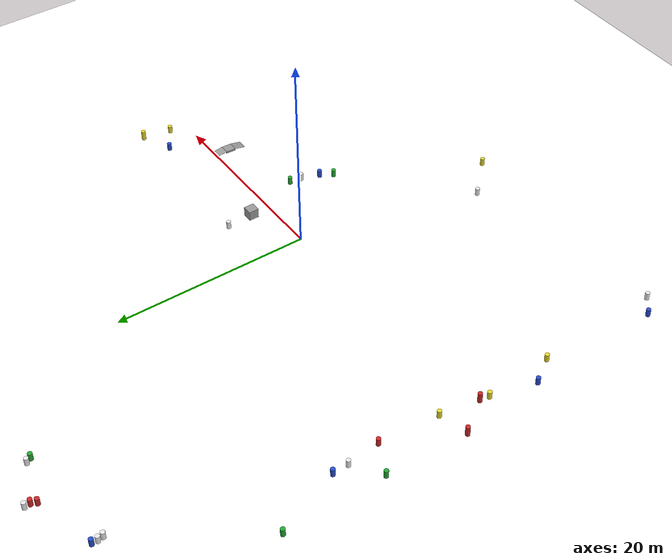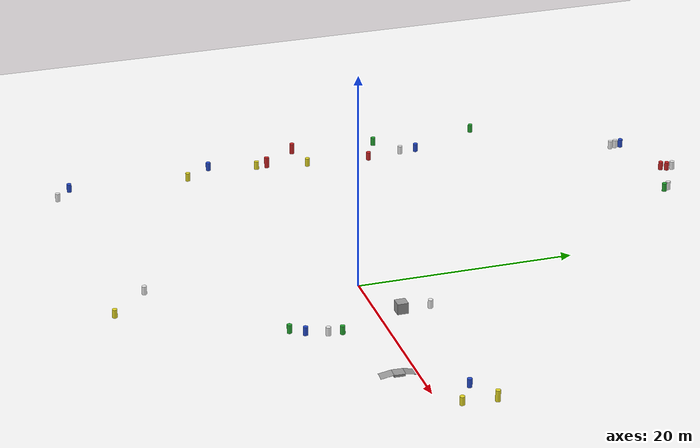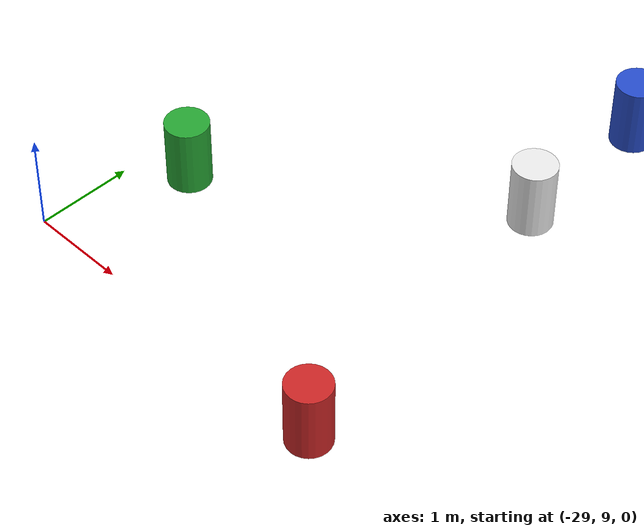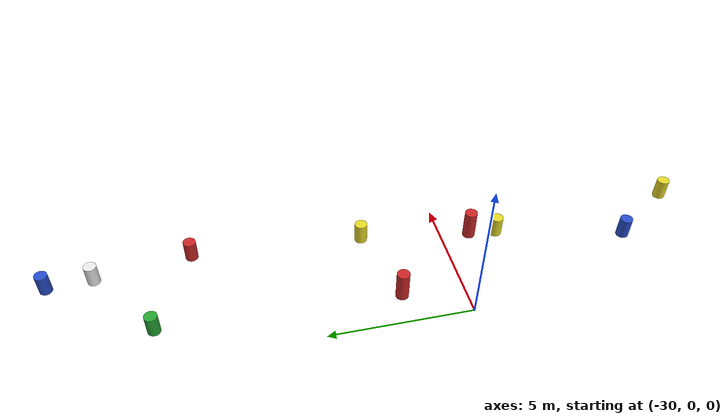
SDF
<sdf version="1.10">
 <world name="IGVC_AutoNav">
  <plugin name="gz::sim::systems::Physics" filename="gz-sim-physics-system"/>
  <plugin name="gz::sim::systems::UserCommands" filename="gz-sim-user-commands-system"/>
  <plugin name="gz::sim::systems::SceneBroadcaster" filename="gz-sim-scene-broadcaster-system"/>
  <plugin name="gz::sim::systems::Contact" filename="gz-sim-contact-system"/>
  <plugin name="gz::sim::systems::NavSat" filename="gz-sim-navsat-system"/>
  <spherical_coordinates>
   <surface_model>EARTH_WGS84</surface_model>
   <world_frame_orientation>ENU</world_frame_orientation>
   <latitude_deg>47.478949999999998</latitude_deg>
   <longitude_deg>19.057784999999999</longitude_deg>
   <elevation>0</elevation>
   <heading_deg>0</heading_deg>
  </spherical_coordinates>
  <plugin name="gz::sim::systems::Sensors" filename="gz-sim-sensors-system">
   <render_engine>ogre2</render_engine>
  </plugin>
  <plugin name="gz::sim::systems::Imu" filename="gz-sim-imu-system"/>
  <plugin name="gz::sim::systems::NavSat" filename="gz-sim-navsat-system"/>
  <gravity>0 0 -9.8000000000000007</gravity>
  <magnetic_field>6.0000000000000002e-06 2.3e-05 -4.1999999999999998e-05</magnetic_field>
  <atmosphere type="adiabatic"/>
  <physics type="ode">
   <max_step_size>0.001</max_step_size>
   <real_time_factor>1</real_time_factor>
   <real_time_update_rate>1000</real_time_update_rate>
  </physics>
  <scene>
   <ambient>0.400000006 0.400000006 0.400000006 1</ambient>
   <background>0.699999988 0.699999988 0.699999988 1</background>
   <shadows>true</shadows>
  </scene>
  <spherical_coordinates>
   <surface_model>EARTH_WGS84</surface_model>
   <latitude_deg>0</latitude_deg>
   <longitude_deg>0</longitude_deg>
   <elevation>0</elevation>
   <heading_deg>0</heading_deg>
  </spherical_coordinates>
  <model name="asphalt_ground_plane">
   <static>true</static>
   <link name="link">
    <collision name="collision">
     <geometry><plane><normal>0 0 1</normal><size>64.748999999999995 67.341999999999999</size></plane></geometry>
     <surface><friction><ode><mu>100</mu><mu2>50</mu2></ode></friction></surface>
    </collision>
    <visual name="visual">
     <cast_shadows>false</cast_shadows>
     <geometry><plane><normal>0 0 1</normal><size>64.748999999999995 67.341999999999999</size></plane></geometry>
     <material>
      <diffuse>1 1 1 1</diffuse>
      <specular>1 1 1 1</specular>
      <pbr><metal><albedo_map>file://media/materials/textures/asphalt.png</albedo_map></metal></pbr>
     </material>
    </visual>
    <inertial>
     <mass>1</mass>
     <inertia><ixx>1</ixx><ixy>0</ixy><ixz>0</ixz><iyy>1</iyy><iyz>0</iyz><izz>1</izz></inertia>
    </inertial>
   </link>
   <pose>0.15136438608169556 7.0954899787902832 0 0 0 0</pose>
  </model>
  <model name="barrel">
   <link name="link">
    <inertial>
     <mass>1</mass>
     <inertia>
      <ixx>0.14583299999999999</ixx>
      <ixy>0</ixy>
      <ixz>0</ixz>
      <iyy>0.14583299999999999</iyy>
      <iyz>0</iyz>
      <izz>0.125</izz>
     </inertia>
    </inertial>
    <visual name="visual">
     <geometry><cylinder><radius>0.222916</radius><length>1.0356700000000001</length></cylinder></geometry>
     <material>
      <script><name>Gazebo/Blue</name><uri>file://media/materials/scripts/gazebo.material</uri></script>
      <shader type="pixel"/>
     </material>
    </visual>
    <collision name="collision">
     <geometry><cylinder><radius>0.222916</radius><length>1.0356700000000001</length></cylinder></geometry>
     <surface>
      <friction>
       <ode><mu>1</mu><mu2>1</mu2><fdir1>0 0 0</fdir1><slip1>0</slip1><slip2>0</slip2></ode>
       <torsional>
        <coefficient>1</coefficient>
        <patch_radius>0</patch_radius>
        <surface_radius>0</surface_radius>
        <use_patch_radius>true</use_patch_radius>
        <ode><slip>0</slip></ode>
       </torsional>
      </friction>
      <bounce><restitution_coefficient>0</restitution_coefficient><threshold>1000000</threshold></bounce>
      <contact>
       <collide_without_contact>false</collide_without_contact>
       <collide_without_contact_bitmask>1</collide_without_contact_bitmask>
       <collide_bitmask>1</collide_bitmask>
       <ode>
        <soft_cfm>0</soft_cfm>
        <soft_erp>0.20000000000000001</soft_erp>
        <kp>10000000000000</kp>
        <kd>1</kd>
        <max_vel>0.01</max_vel>
        <min_depth>0</min_depth>
       </ode>
       <bullet>
        <split_impulse>true</split_impulse>
        <split_impulse_penetration_threshold>-0.01</split_impulse_penetration_threshold>
        <soft_cfm>0</soft_cfm>
        <soft_erp>0.20000000000000001</soft_erp>
        <kp>10000000000000</kp>
        <kd>1</kd>
       </bullet>
      </contact>
     </surface>
    </collision>
   </link>
   <static>false</static>
   <pose>7.06515 -6.9198300000000001 0.19306669072640001 -1.3752199554967039e-16 1.8690165760576609e-16 4.860942391092337e-19</pose>
  </model>
  <model name="barrel_0">
   <link name="link">
    <inertial>
     <mass>1</mass>
     <inertia>
      <ixx>0.14583299999999999</ixx>
      <ixy>0</ixy>
      <ixz>0</ixz>
      <iyy>0.14583299999999999</iyy>
      <iyz>0</iyz>
      <izz>0.125</izz>
     </inertia>
    </inertial>
    <visual name="visual">
     <geometry><cylinder><radius>0.222916</radius><length>1.0356700000000001</length></cylinder></geometry>
     <material>
      <script><name>Gazebo/Green</name><uri>file://media/materials/scripts/gazebo.material</uri></script>
      <shader type="pixel"/>
     </material>
    </visual>
    <collision name="collision">
     <geometry><cylinder><radius>0.222916</radius><length>1.0356700000000001</length></cylinder></geometry>
     <surface>
      <friction>
       <ode><mu>1</mu><mu2>1</mu2><fdir1>0 0 0</fdir1><slip1>0</slip1><slip2>0</slip2></ode>
       <torsional>
        <coefficient>1</coefficient>
        <patch_radius>0</patch_radius>
        <surface_radius>0</surface_radius>
        <use_patch_radius>true</use_patch_radius>
        <ode><slip>0</slip></ode>
       </torsional>
      </friction>
      <bounce><restitution_coefficient>0</restitution_coefficient><threshold>1000000</threshold></bounce>
      <contact>
       <collide_without_contact>false</collide_without_contact>
       <collide_without_contact_bitmask>1</collide_without_contact_bitmask>
       <collide_bitmask>1</collide_bitmask>
       <ode>
        <soft_cfm>0</soft_cfm>
        <soft_erp>0.20000000000000001</soft_erp>
        <kp>10000000000000</kp>
        <kd>1</kd>
        <max_vel>0.01</max_vel>
        <min_depth>0</min_depth>
       </ode>
       <bullet>
        <split_impulse>true</split_impulse>
        <split_impulse_penetration_threshold>-0.01</split_impulse_penetration_threshold>
        <soft_cfm>0</soft_cfm>
        <soft_erp>0.20000000000000001</soft_erp>
        <kp>10000000000000</kp>
        <kd>1</kd>
       </bullet>
      </contact>
     </surface>
    </collision>
   </link>
   <static>false</static>
   <pose>6.2997100000000001 -8.1233199999999997 0.19307069065783897 -1.7394015606776851e-16 1.6237547592391612e-16 2.9792624961899897e-20</pose>
  </model>
  <model name="barrel_3">
   <link name="link">
    <inertial>
     <mass>1</mass>
     <inertia>
      <ixx>0.14583299999999999</ixx>
      <ixy>0</ixy>
      <ixz>0</ixz>
      <iyy>0.14583299999999999</iyy>
      <iyz>0</iyz>
      <izz>0.125</izz>
     </inertia>
    </inertial>
    <visual name="visual">
     <geometry><cylinder><radius>0.222916</radius><length>1.0356700000000001</length></cylinder></geometry>
     <material>
      <script><name>Gazebo/White</name><uri>file://media/materials/scripts/gazebo.material</uri></script>
      <shader type="pixel"/>
     </material>
    </visual>
    <collision name="collision">
     <geometry><cylinder><radius>0.222916</radius><length>1.0356700000000001</length></cylinder></geometry>
     <surface>
      <friction>
       <ode><mu>1</mu><mu2>1</mu2><fdir1>0 0 0</fdir1><slip1>0</slip1><slip2>0</slip2></ode>
       <torsional>
        <coefficient>1</coefficient>
        <patch_radius>0</patch_radius>
        <surface_radius>0</surface_radius>
        <use_patch_radius>true</use_patch_radius>
        <ode><slip>0</slip></ode>
       </torsional>
      </friction>
      <bounce><restitution_coefficient>0</restitution_coefficient><threshold>1000000</threshold></bounce>
      <contact>
       <collide_without_contact>false</collide_without_contact>
       <collide_without_contact_bitmask>1</collide_without_contact_bitmask>
       <collide_bitmask>1</collide_bitmask>
       <ode>
        <soft_cfm>0</soft_cfm>
        <soft_erp>0.20000000000000001</soft_erp>
        <kp>10000000000000</kp>
        <kd>1</kd>
        <max_vel>0.01</max_vel>
        <min_depth>0</min_depth>
       </ode>
       <bullet>
        <split_impulse>true</split_impulse>
        <split_impulse_penetration_threshold>-0.01</split_impulse_penetration_threshold>
        <soft_cfm>0</soft_cfm>
        <soft_erp>0.20000000000000001</soft_erp>
        <kp>10000000000000</kp>
        <kd>1</kd>
       </bullet>
      </contact>
     </surface>
    </collision>
   </link>
   <static>false</static>
   <pose>-20.715963363647461 32.357498168945312 0.19150133251402368 -1.5630929914832792e-16 -7.2520117303603423e-17 1.9488451680036415e-18</pose>
  </model>
  <model name="barrel_4">
   <link name="link">
    <inertial>
     <mass>1</mass>
     <inertia>
      <ixx>0.14583299999999999</ixx>
      <ixy>0</ixy>
      <ixz>0</ixz>
      <iyy>0.14583299999999999</iyy>
      <iyz>0</iyz>
      <izz>0.125</izz>
     </inertia>
    </inertial>
    <visual name="visual">
     <geometry><cylinder><radius>0.222916</radius><length>1.0356700000000001</length></cylinder></geometry>
     <material>
      <script><name>Gazebo/White</name><uri>file://media/materials/scripts/gazebo.material</uri></script>
      <shader type="pixel"/>
     </material>
    </visual>
    <collision name="collision">
     <geometry><cylinder><radius>0.222916</radius><length>1.0356700000000001</length></cylinder></geometry>
     <surface>
      <friction>
       <ode><mu>1</mu><mu2>1</mu2><fdir1>0 0 0</fdir1><slip1>0</slip1><slip2>0</slip2></ode>
       <torsional>
        <coefficient>1</coefficient>
        <patch_radius>0</patch_radius>
        <surface_radius>0</surface_radius>
        <use_patch_radius>true</use_patch_radius>
        <ode><slip>0</slip></ode>
       </torsional>
      </friction>
      <bounce><restitution_coefficient>0</restitution_coefficient><threshold>1000000</threshold></bounce>
      <contact>
       <collide_without_contact>false</collide_without_contact>
       <collide_without_contact_bitmask>1</collide_without_contact_bitmask>
       <collide_bitmask>1</collide_bitmask>
       <ode>
        <soft_cfm>0</soft_cfm>
        <soft_erp>0.20000000000000001</soft_erp>
        <kp>10000000000000</kp>
        <kd>1</kd>
        <max_vel>0.01</max_vel>
        <min_depth>0</min_depth>
       </ode>
       <bullet>
        <split_impulse>true</split_impulse>
        <split_impulse_penetration_threshold>-0.01</split_impulse_penetration_threshold>
        <soft_cfm>0</soft_cfm>
        <soft_erp>0.20000000000000001</soft_erp>
        <kp>10000000000000</kp>
        <kd>1</kd>
       </bullet>
      </contact>
     </surface>
    </collision>
   </link>
   <static>false</static>
   <pose>-25.243345260620117 -21.755100250244141 0.19173168667276036 2.1714277532571481e-16 -9.726870776891949e-17 -2.3794293549420035e-18</pose>
  </model>
  <model name="barrel_5">
   <link name="link">
    <inertial>
     <mass>1</mass>
     <inertia>
      <ixx>0.14583299999999999</ixx>
      <ixy>0</ixy>
      <ixz>0</ixz>
      <iyy>0.14583299999999999</iyy>
      <iyz>0</iyz>
      <izz>0.125</izz>
     </inertia>
    </inertial>
    <visual name="visual">
     <geometry><cylinder><radius>0.222916</radius><length>1.0356700000000001</length></cylinder></geometry>
     <material>
      <script><name>Gazebo/Yellow</name><uri>file://media/materials/scripts/gazebo.material</uri></script>
      <shader type="pixel"/>
     </material>
    </visual>
    <collision name="collision">
     <geometry><cylinder><radius>0.222916</radius><length>1.0356700000000001</length></cylinder></geometry>
     <surface>
      <friction>
       <ode><mu>1</mu><mu2>1</mu2><fdir1>0 0 0</fdir1><slip1>0</slip1><slip2>0</slip2></ode>
       <torsional>
        <coefficient>1</coefficient>
        <patch_radius>0</patch_radius>
        <surface_radius>0</surface_radius>
        <use_patch_radius>true</use_patch_radius>
        <ode><slip>0</slip></ode>
       </torsional>
      </friction>
      <bounce><restitution_coefficient>0</restitution_coefficient><threshold>1000000</threshold></bounce>
      <contact>
       <collide_without_contact>false</collide_without_contact>
       <collide_without_contact_bitmask>1</collide_without_contact_bitmask>
       <collide_bitmask>1</collide_bitmask>
       <ode>
        <soft_cfm>0</soft_cfm>
        <soft_erp>0.20000000000000001</soft_erp>
        <kp>10000000000000</kp>
        <kd>1</kd>
        <max_vel>0.01</max_vel>
        <min_depth>0</min_depth>
       </ode>
       <bullet>
        <split_impulse>true</split_impulse>
        <split_impulse_penetration_threshold>-0.01</split_impulse_penetration_threshold>
        <soft_cfm>0</soft_cfm>
        <soft_erp>0.20000000000000001</soft_erp>
        <kp>10000000000000</kp>
        <kd>1</kd>
       </bullet>
      </contact>
     </surface>
    </collision>
   </link>
   <static>false</static>
   <pose>-25.960578918457031 -8.9916601181030273 0.1925797060489432 2.513793420743785e-16 -6.5764378003597088e-17 -4.2133545942458071e-19</pose>
  </model>
  <model name="barrel_7">
   <link name="link">
    <inertial>
     <mass>1</mass>
     <inertia>
      <ixx>0.14583299999999999</ixx>
      <ixy>0</ixy>
      <ixz>0</ixz>
      <iyy>0.14583299999999999</iyy>
      <iyz>0</iyz>
      <izz>0.125</izz>
     </inertia>
    </inertial>
    <visual name="visual">
     <geometry><cylinder><radius>0.222916</radius><length>1.0356700000000001</length></cylinder></geometry>
     <material>
      <script><name>Gazebo/Blue</name><uri>file://media/materials/scripts/gazebo.material</uri></script>
      <shader type="pixel"/>
     </material>
    </visual>
    <collision name="collision">
     <geometry><cylinder><radius>0.222916</radius><length>1.0356700000000001</length></cylinder></geometry>
     <surface>
      <friction>
       <ode><mu>1</mu><mu2>1</mu2><fdir1>0 0 0</fdir1><slip1>0</slip1><slip2>0</slip2></ode>
       <torsional>
        <coefficient>1</coefficient>
        <patch_radius>0</patch_radius>
        <surface_radius>0</surface_radius>
        <use_patch_radius>true</use_patch_radius>
        <ode><slip>0</slip></ode>
       </torsional>
      </friction>
      <bounce><restitution_coefficient>0</restitution_coefficient><threshold>1000000</threshold></bounce>
      <contact>
       <collide_without_contact>false</collide_without_contact>
       <collide_without_contact_bitmask>1</collide_without_contact_bitmask>
       <collide_bitmask>1</collide_bitmask>
       <ode>
        <soft_cfm>0</soft_cfm>
        <soft_erp>0.20000000000000001</soft_erp>
        <kp>10000000000000</kp>
        <kd>1</kd>
        <max_vel>0.01</max_vel>
        <min_depth>0</min_depth>
       </ode>
       <bullet>
        <split_impulse>true</split_impulse>
        <split_impulse_penetration_threshold>-0.01</split_impulse_penetration_threshold>
        <soft_cfm>0</soft_cfm>
        <soft_erp>0.20000000000000001</soft_erp>
        <kp>10000000000000</kp>
        <kd>1</kd>
       </bullet>
      </contact>
     </surface>
    </collision>
   </link>
   <static>false</static>
   <pose>-27.665267944335938 -6.5483798980712891 0.19243568848058651 -1.6089329342709861e-16 -3.1167044410026668e-16 2.4590483089812842e-18</pose>
  </model>
  <model name="barrel_8">
   <link name="link">
    <inertial>
     <mass>1</mass>
     <inertia>
      <ixx>0.14583299999999999</ixx>
      <ixy>0</ixy>
      <ixz>0</ixz>
      <iyy>0.14583299999999999</iyy>
      <iyz>0</iyz>
      <izz>0.125</izz>
     </inertia>
    </inertial>
    <visual name="visual">
     <geometry><cylinder><radius>0.222916</radius><length>1.0356700000000001</length></cylinder></geometry>
     <material>
      <script><name>Gazebo/White</name><uri>file://media/materials/scripts/gazebo.material</uri></script>
      <shader type="pixel"/>
     </material>
    </visual>
    <collision name="collision">
     <geometry><cylinder><radius>0.222916</radius><length>1.0356700000000001</length></cylinder></geometry>
     <surface>
      <friction>
       <ode><mu>1</mu><mu2>1</mu2><fdir1>0 0 0</fdir1><slip1>0</slip1><slip2>0</slip2></ode>
       <torsional>
        <coefficient>1</coefficient>
        <patch_radius>0</patch_radius>
        <surface_radius>0</surface_radius>
        <use_patch_radius>true</use_patch_radius>
        <ode><slip>0</slip></ode>
       </torsional>
      </friction>
      <bounce><restitution_coefficient>0</restitution_coefficient><threshold>1000000</threshold></bounce>
      <contact>
       <collide_without_contact>false</collide_without_contact>
       <collide_without_contact_bitmask>1</collide_without_contact_bitmask>
       <collide_bitmask>1</collide_bitmask>
       <ode>
        <soft_cfm>0</soft_cfm>
        <soft_erp>0.20000000000000001</soft_erp>
        <kp>10000000000000</kp>
        <kd>1</kd>
        <max_vel>0.01</max_vel>
        <min_depth>0</min_depth>
       </ode>
       <bullet>
        <split_impulse>true</split_impulse>
        <split_impulse_penetration_threshold>-0.01</split_impulse_penetration_threshold>
        <soft_cfm>0</soft_cfm>
        <soft_erp>0.20000000000000001</soft_erp>
        <kp>10000000000000</kp>
        <kd>1</kd>
       </bullet>
      </contact>
     </surface>
    </collision>
   </link>
   <static>false</static>
   <pose>-4.3687233924865723 -18.289100646972656 0.19028669984245494 -1.9536287786089899e-16 2.0452711614225613e-17 1.2133117316470607e-18</pose>
  </model>
  <model name="barrel_10">
   <link name="link">
    <inertial>
     <mass>1</mass>
     <inertia>
      <ixx>0.14583299999999999</ixx>
      <ixy>0</ixy>
      <ixz>0</ixz>
      <iyy>0.14583299999999999</iyy>
      <iyz>0</iyz>
      <izz>0.125</izz>
     </inertia>
    </inertial>
    <visual name="visual">
     <geometry><cylinder><radius>0.222916</radius><length>1.0356700000000001</length></cylinder></geometry>
     <material>
      <script><name>Gazebo/Blue</name><uri>file://media/materials/scripts/gazebo.material</uri></script>
      <shader type="pixel"/>
     </material>
    </visual>
    <collision name="collision">
     <geometry><cylinder><radius>0.222916</radius><length>1.0356700000000001</length></cylinder></geometry>
     <surface>
      <friction>
       <ode><mu>1</mu><mu2>1</mu2><fdir1>0 0 0</fdir1><slip1>0</slip1><slip2>0</slip2></ode>
       <torsional>
        <coefficient>1</coefficient>
        <patch_radius>0</patch_radius>
        <surface_radius>0</surface_radius>
        <use_patch_radius>true</use_patch_radius>
        <ode><slip>0</slip></ode>
       </torsional>
      </friction>
      <bounce><restitution_coefficient>0</restitution_coefficient><threshold>1000000</threshold></bounce>
      <contact>
       <collide_without_contact>false</collide_without_contact>
       <collide_without_contact_bitmask>1</collide_without_contact_bitmask>
       <collide_bitmask>1</collide_bitmask>
       <ode>
        <soft_cfm>0</soft_cfm>
        <soft_erp>0.20000000000000001</soft_erp>
        <kp>10000000000000</kp>
        <kd>1</kd>
        <max_vel>0.01</max_vel>
        <min_depth>0</min_depth>
       </ode>
       <bullet>
        <split_impulse>true</split_impulse>
        <split_impulse_penetration_threshold>-0.01</split_impulse_penetration_threshold>
        <soft_cfm>0</soft_cfm>
        <soft_erp>0.20000000000000001</soft_erp>
        <kp>10000000000000</kp>
        <kd>1</kd>
       </bullet>
      </contact>
     </surface>
    </collision>
   </link>
   <static>false</static>
   <pose>-25.850784301757812 13.89840030670166 0.19229074835595733 -1.7448716400180568e-16 -1.9643319622429089e-17 1.5948232934256708e-18</pose>
  </model>
  <model name="barrel_11">
   <link name="link">
    <inertial>
     <mass>1</mass>
     <inertia>
      <ixx>0.14583299999999999</ixx>
      <ixy>0</ixy>
      <ixz>0</ixz>
      <iyy>0.14583299999999999</iyy>
      <iyz>0</iyz>
      <izz>0.125</izz>
     </inertia>
    </inertial>
    <visual name="visual">
     <geometry><cylinder><radius>0.222916</radius><length>1.0356700000000001</length></cylinder></geometry>
     <material>
      <script><name>Gazebo/Yellow</name><uri>file://media/materials/scripts/gazebo.material</uri></script>
      <shader type="pixel"/>
     </material>
    </visual>
    <collision name="collision">
     <geometry><cylinder><radius>0.222916</radius><length>1.0356700000000001</length></cylinder></geometry>
     <surface>
      <friction>
       <ode><mu>1</mu><mu2>1</mu2><fdir1>0 0 0</fdir1><slip1>0</slip1><slip2>0</slip2></ode>
       <torsional>
        <coefficient>1</coefficient>
        <patch_radius>0</patch_radius>
        <surface_radius>0</surface_radius>
        <use_patch_radius>true</use_patch_radius>
        <ode><slip>0</slip></ode>
       </torsional>
      </friction>
      <bounce><restitution_coefficient>0</restitution_coefficient><threshold>1000000</threshold></bounce>
      <contact>
       <collide_without_contact>false</collide_without_contact>
       <collide_without_contact_bitmask>1</collide_without_contact_bitmask>
       <collide_bitmask>1</collide_bitmask>
       <ode>
        <soft_cfm>0</soft_cfm>
        <soft_erp>0.20000000000000001</soft_erp>
        <kp>10000000000000</kp>
        <kd>1</kd>
        <max_vel>0.01</max_vel>
        <min_depth>0</min_depth>
       </ode>
       <bullet>
        <split_impulse>true</split_impulse>
        <split_impulse_penetration_threshold>-0.01</split_impulse_penetration_threshold>
        <soft_cfm>0</soft_cfm>
        <soft_erp>0.20000000000000001</soft_erp>
        <kp>10000000000000</kp>
        <kd>1</kd>
       </bullet>
      </contact>
     </surface>
    </collision>
   </link>
   <static>false</static>
   <pose>-26.542016983032227 -2.0249800682067871 0.19150812449045673 -1.881317086243172e-16 1.4487575548300299e-16 2.7783390687428676e-18</pose>
  </model>
  <model name="barrel_13">
   <link name="link">
    <inertial>
     <mass>1</mass>
     <inertia>
      <ixx>0.14583299999999999</ixx>
      <ixy>0</ixy>
      <ixz>0</ixz>
      <iyy>0.14583299999999999</iyy>
      <iyz>0</iyz>
      <izz>0.125</izz>
     </inertia>
    </inertial>
    <visual name="visual">
     <geometry><cylinder><radius>0.222916</radius><length>1.0356700000000001</length></cylinder></geometry>
     <material>
      <script><name>Gazebo/Green</name><uri>file://media/materials/scripts/gazebo.material</uri></script>
      <shader type="pixel"/>
     </material>
    </visual>
    <collision name="collision">
     <geometry><cylinder><radius>0.222916</radius><length>1.0356700000000001</length></cylinder></geometry>
     <surface>
      <friction>
       <ode><mu>1</mu><mu2>1</mu2><fdir1>0 0 0</fdir1><slip1>0</slip1><slip2>0</slip2></ode>
       <torsional>
        <coefficient>1</coefficient>
        <patch_radius>0</patch_radius>
        <surface_radius>0</surface_radius>
        <use_patch_radius>true</use_patch_radius>
        <ode><slip>0</slip></ode>
       </torsional>
      </friction>
      <bounce><restitution_coefficient>0</restitution_coefficient><threshold>1000000</threshold></bounce>
      <contact>
       <collide_without_contact>false</collide_without_contact>
       <collide_without_contact_bitmask>1</collide_without_contact_bitmask>
       <collide_bitmask>1</collide_bitmask>
       <ode>
        <soft_cfm>0</soft_cfm>
        <soft_erp>0.20000000000000001</soft_erp>
        <kp>10000000000000</kp>
        <kd>1</kd>
        <max_vel>0.01</max_vel>
        <min_depth>0</min_depth>
       </ode>
       <bullet>
        <split_impulse>true</split_impulse>
        <split_impulse_penetration_threshold>-0.01</split_impulse_penetration_threshold>
        <soft_cfm>0</soft_cfm>
        <soft_erp>0.20000000000000001</soft_erp>
        <kp>10000000000000</kp>
        <kd>1</kd>
       </bullet>
      </contact>
     </surface>
    </collision>
   </link>
   <static>false</static>
   <pose>-28.592302322387695 20.560400009155273 0.19208067378286536 2.167474750067388e-16 -3.8483230633916584e-17 -5.098448913254874e-18</pose>
  </model>
  <model name="barrel_14">
   <link name="link">
    <inertial>
     <mass>1</mass>
     <inertia>
      <ixx>0.14583299999999999</ixx>
      <ixy>0</ixy>
      <ixz>0</ixz>
      <iyy>0.14583299999999999</iyy>
      <iyz>0</iyz>
      <izz>0.125</izz>
     </inertia>
    </inertial>
    <visual name="visual">
     <geometry><cylinder><radius>0.222916</radius><length>1.0356700000000001</length></cylinder></geometry>
     <material>
      <script><name>Gazebo/Red</name><uri>file://media/materials/scripts/gazebo.material</uri></script>
      <shader type="pixel"/>
     </material>
    </visual>
    <collision name="collision">
     <geometry><cylinder><radius>0.222916</radius><length>1.0356700000000001</length></cylinder></geometry>
     <surface>
      <friction>
       <ode><mu>1</mu><mu2>1</mu2><fdir1>0 0 0</fdir1><slip1>0</slip1><slip2>0</slip2></ode>
       <torsional>
        <coefficient>1</coefficient>
        <patch_radius>0</patch_radius>
        <surface_radius>0</surface_radius>
        <use_patch_radius>true</use_patch_radius>
        <ode><slip>0</slip></ode>
       </torsional>
      </friction>
      <bounce><restitution_coefficient>0</restitution_coefficient><threshold>1000000</threshold></bounce>
      <contact>
       <collide_without_contact>false</collide_without_contact>
       <collide_without_contact_bitmask>1</collide_without_contact_bitmask>
       <collide_bitmask>1</collide_bitmask>
       <ode>
        <soft_cfm>0</soft_cfm>
        <soft_erp>0.20000000000000001</soft_erp>
        <kp>10000000000000</kp>
        <kd>1</kd>
        <max_vel>0.01</max_vel>
        <min_depth>0</min_depth>
       </ode>
       <bullet>
        <split_impulse>true</split_impulse>
        <split_impulse_penetration_threshold>-0.01</split_impulse_penetration_threshold>
        <soft_cfm>0</soft_cfm>
        <soft_erp>0.20000000000000001</soft_erp>
        <kp>10000000000000</kp>
        <kd>1</kd>
       </bullet>
      </contact>
     </surface>
    </collision>
   </link>
   <static>false</static>
   <pose>-25.332365036010742 8.9310302734375 0.19230267921328187 7.7129886615495359e-17 7.5269650063022334e-17 2.1738360060126336e-18</pose>
  </model>
  <model name="barrel_15">
   <link name="link">
    <inertial>
     <mass>1</mass>
     <inertia>
      <ixx>0.14583299999999999</ixx>
      <ixy>0</ixy>
      <ixz>0</ixz>
      <iyy>0.14583299999999999</iyy>
      <iyz>0</iyz>
      <izz>0.125</izz>
     </inertia>
    </inertial>
    <visual name="visual">
     <geometry><cylinder><radius>0.222916</radius><length>1.0356700000000001</length></cylinder></geometry>
     <material>
      <script><name>Gazebo/White</name><uri>file://media/materials/scripts/gazebo.material</uri></script>
      <shader type="pixel"/>
     </material>
    </visual>
    <collision name="collision">
     <geometry><cylinder><radius>0.222916</radius><length>1.0356700000000001</length></cylinder></geometry>
     <surface>
      <friction>
       <ode><mu>1</mu><mu2>1</mu2><fdir1>0 0 0</fdir1><slip1>0</slip1><slip2>0</slip2></ode>
       <torsional>
        <coefficient>1</coefficient>
        <patch_radius>0</patch_radius>
        <surface_radius>0</surface_radius>
        <use_patch_radius>true</use_patch_radius>
        <ode><slip>0</slip></ode>
       </torsional>
      </friction>
      <bounce><restitution_coefficient>0</restitution_coefficient><threshold>1000000</threshold></bounce>
      <contact>
       <collide_without_contact>false</collide_without_contact>
       <collide_without_contact_bitmask>1</collide_without_contact_bitmask>
       <collide_bitmask>1</collide_bitmask>
       <ode>
        <soft_cfm>0</soft_cfm>
        <soft_erp>0.20000000000000001</soft_erp>
        <kp>10000000000000</kp>
        <kd>1</kd>
        <max_vel>0.01</max_vel>
        <min_depth>0</min_depth>
       </ode>
       <bullet>
        <split_impulse>true</split_impulse>
        <split_impulse_penetration_threshold>-0.01</split_impulse_penetration_threshold>
        <soft_cfm>0</soft_cfm>
        <soft_erp>0.20000000000000001</soft_erp>
        <kp>10000000000000</kp>
        <kd>1</kd>
       </bullet>
      </contact>
     </surface>
    </collision>
   </link>
   <static>false</static>
   <pose>-25.783918380737305 12.307399749755859 0.19236870516492593 -2.1647209022431466e-16 -2.405290214608294e-16 -2.4143132996556886e-18</pose>
  </model>
  <model name="barrel_16">
   <link name="link">
    <inertial>
     <mass>1</mass>
     <inertia>
      <ixx>0.14583299999999999</ixx>
      <ixy>0</ixy>
      <ixz>0</ixz>
      <iyy>0.14583299999999999</iyy>
      <iyz>0</iyz>
      <izz>0.125</izz>
     </inertia>
    </inertial>
    <visual name="visual">
     <geometry><cylinder><radius>0.222916</radius><length>1.0356700000000001</length></cylinder></geometry>
     <material>
      <script><name>Gazebo/Yellow</name><uri>file://media/materials/scripts/gazebo.material</uri></script>
      <shader type="pixel"/>
     </material>
    </visual>
    <collision name="collision">
     <geometry><cylinder><radius>0.222916</radius><length>1.0356700000000001</length></cylinder></geometry>
     <surface>
      <friction>
       <ode><mu>1</mu><mu2>1</mu2><fdir1>0 0 0</fdir1><slip1>0</slip1><slip2>0</slip2></ode>
       <torsional>
        <coefficient>1</coefficient>
        <patch_radius>0</patch_radius>
        <surface_radius>0</surface_radius>
        <use_patch_radius>true</use_patch_radius>
        <ode><slip>0</slip></ode>
       </torsional>
      </friction>
      <bounce><restitution_coefficient>0</restitution_coefficient><threshold>1000000</threshold></bounce>
      <contact>
       <collide_without_contact>false</collide_without_contact>
       <collide_without_contact_bitmask>1</collide_without_contact_bitmask>
       <collide_bitmask>1</collide_bitmask>
       <ode>
        <soft_cfm>0</soft_cfm>
        <soft_erp>0.20000000000000001</soft_erp>
        <kp>10000000000000</kp>
        <kd>1</kd>
        <max_vel>0.01</max_vel>
        <min_depth>0</min_depth>
       </ode>
       <bullet>
        <split_impulse>true</split_impulse>
        <split_impulse_penetration_threshold>-0.01</split_impulse_penetration_threshold>
        <soft_cfm>0</soft_cfm>
        <soft_erp>0.20000000000000001</soft_erp>
        <kp>10000000000000</kp>
        <kd>1</kd>
       </bullet>
      </contact>
     </surface>
    </collision>
   </link>
   <static>false</static>
   <pose>-25.781974792480469 2.863569974899292 0.19219966752349077 -2.1661158449713622e-16 1.0497966789318482e-16 6.1598770859728902e-20</pose>
  </model>
  <model name="barrel_22">
   <link name="link">
    <inertial>
     <mass>1</mass>
     <inertia>
      <ixx>0.14583299999999999</ixx>
      <ixy>0</ixy>
      <ixz>0</ixz>
      <iyy>0.14583299999999999</iyy>
      <iyz>0</iyz>
      <izz>0.125</izz>
     </inertia>
    </inertial>
    <visual name="visual">
     <geometry><cylinder><radius>0.222916</radius><length>1.0356700000000001</length></cylinder></geometry>
     <material>
      <script><name>Gazebo/White</name><uri>file://media/materials/scripts/gazebo.material</uri></script>
      <shader type="pixel"/>
     </material>
    </visual>
    <collision name="collision">
     <geometry><cylinder><radius>0.222916</radius><length>1.0356700000000001</length></cylinder></geometry>
     <surface>
      <friction>
       <ode><mu>1</mu><mu2>1</mu2><fdir1>0 0 0</fdir1><slip1>0</slip1><slip2>0</slip2></ode>
       <torsional>
        <coefficient>1</coefficient>
        <patch_radius>0</patch_radius>
        <surface_radius>0</surface_radius>
        <use_patch_radius>true</use_patch_radius>
        <ode><slip>0</slip></ode>
       </torsional>
      </friction>
      <bounce><restitution_coefficient>0</restitution_coefficient><threshold>1000000</threshold></bounce>
      <contact>
       <collide_without_contact>false</collide_without_contact>
       <collide_without_contact_bitmask>1</collide_without_contact_bitmask>
       <collide_bitmask>1</collide_bitmask>
       <ode>
        <soft_cfm>0</soft_cfm>
        <soft_erp>0.20000000000000001</soft_erp>
        <kp>10000000000000</kp>
        <kd>1</kd>
        <max_vel>0.01</max_vel>
        <min_depth>0</min_depth>
       </ode>
       <bullet>
        <split_impulse>true</split_impulse>
        <split_impulse_penetration_threshold>-0.01</split_impulse_penetration_threshold>
        <soft_cfm>0</soft_cfm>
        <soft_erp>0.20000000000000001</soft_erp>
        <kp>10000000000000</kp>
        <kd>1</kd>
       </bullet>
      </contact>
     </surface>
    </collision>
   </link>
   <static>false</static>
   <pose>-14.483590126037598 36.203399658203125 0.19211263195945028 -5.4532423447004407e-18 -7.7421179951692395e-17 1.4523870029707114e-18</pose>
  </model>
  <model name="barrel_23">
   <link name="link">
    <inertial>
     <mass>1</mass>
     <inertia>
      <ixx>0.14583299999999999</ixx>
      <ixy>0</ixy>
      <ixz>0</ixz>
      <iyy>0.14583299999999999</iyy>
      <iyz>0</iyz>
      <izz>0.125</izz>
     </inertia>
    </inertial>
    <visual name="visual">
     <geometry><cylinder><radius>0.222916</radius><length>1.0356700000000001</length></cylinder></geometry>
     <material>
      <script><name>Gazebo/Green</name><uri>file://media/materials/scripts/gazebo.material</uri></script>
      <shader type="pixel"/>
     </material>
    </visual>
    <collision name="collision">
     <geometry><cylinder><radius>0.222916</radius><length>1.0356700000000001</length></cylinder></geometry>
     <surface>
      <friction>
       <ode><mu>1</mu><mu2>1</mu2><fdir1>0 0 0</fdir1><slip1>0</slip1><slip2>0</slip2></ode>
       <torsional>
        <coefficient>1</coefficient>
        <patch_radius>0</patch_radius>
        <surface_radius>0</surface_radius>
        <use_patch_radius>true</use_patch_radius>
        <ode><slip>0</slip></ode>
       </torsional>
      </friction>
      <bounce><restitution_coefficient>0</restitution_coefficient><threshold>1000000</threshold></bounce>
      <contact>
       <collide_without_contact>false</collide_without_contact>
       <collide_without_contact_bitmask>1</collide_without_contact_bitmask>
       <collide_bitmask>1</collide_bitmask>
       <ode>
        <soft_cfm>0</soft_cfm>
        <soft_erp>0.20000000000000001</soft_erp>
        <kp>10000000000000</kp>
        <kd>1</kd>
        <max_vel>0.01</max_vel>
        <min_depth>0</min_depth>
       </ode>
       <bullet>
        <split_impulse>true</split_impulse>
        <split_impulse_penetration_threshold>-0.01</split_impulse_penetration_threshold>
        <soft_cfm>0</soft_cfm>
        <soft_erp>0.20000000000000001</soft_erp>
        <kp>10000000000000</kp>
        <kd>1</kd>
       </bullet>
      </contact>
     </surface>
    </collision>
   </link>
   <static>false</static>
   <pose>-28.489200592041016 10.397676467895508 0.19137015809615299 -1.1145704170559984e-16 -8.4349744873123274e-17 8.6370781010305068e-19</pose>
  </model>
  <model name="barrel_24">
   <link name="link">
    <inertial>
     <mass>1</mass>
     <inertia>
      <ixx>0.14583299999999999</ixx>
      <ixy>0</ixy>
      <ixz>0</ixz>
      <iyy>0.14583299999999999</iyy>
      <iyz>0</iyz>
      <izz>0.125</izz>
     </inertia>
    </inertial>
    <visual name="visual">
     <geometry><cylinder><radius>0.222916</radius><length>1.0356700000000001</length></cylinder></geometry>
     <material>
      <script><name>Gazebo/White</name><uri>file://media/materials/scripts/gazebo.material</uri></script>
      <shader type="pixel"/>
     </material>
    </visual>
    <collision name="collision">
     <geometry><cylinder><radius>0.222916</radius><length>1.0356700000000001</length></cylinder></geometry>
     <surface>
      <friction>
       <ode><mu>1</mu><mu2>1</mu2><fdir1>0 0 0</fdir1><slip1>0</slip1><slip2>0</slip2></ode>
       <torsional>
        <coefficient>1</coefficient>
        <patch_radius>0</patch_radius>
        <surface_radius>0</surface_radius>
        <use_patch_radius>true</use_patch_radius>
        <ode><slip>0</slip></ode>
       </torsional>
      </friction>
      <bounce><restitution_coefficient>0</restitution_coefficient><threshold>1000000</threshold></bounce>
      <contact>
       <collide_without_contact>false</collide_without_contact>
       <collide_without_contact_bitmask>1</collide_without_contact_bitmask>
       <collide_bitmask>1</collide_bitmask>
       <ode>
        <soft_cfm>0</soft_cfm>
        <soft_erp>0.20000000000000001</soft_erp>
        <kp>10000000000000</kp>
        <kd>1</kd>
        <max_vel>0.01</max_vel>
        <min_depth>0</min_depth>
       </ode>
       <bullet>
        <split_impulse>true</split_impulse>
        <split_impulse_penetration_threshold>-0.01</split_impulse_penetration_threshold>
        <soft_cfm>0</soft_cfm>
        <soft_erp>0.20000000000000001</soft_erp>
        <kp>10000000000000</kp>
        <kd>1</kd>
       </bullet>
      </contact>
     </surface>
    </collision>
   </link>
   <static>false</static>
   <pose>-10.382210731506348 34.021999359130859 0.19137045289728427 6.041603864123488e-17 -1.5710058991408846e-16 1.0253059965267708e-18</pose>
  </model>
  <model name="barrel_26">
   <link name="link">
    <inertial>
     <mass>1</mass>
     <inertia>
      <ixx>0.14583299999999999</ixx>
      <ixy>0</ixy>
      <ixz>0</ixz>
      <iyy>0.14583299999999999</iyy>
      <iyz>0</iyz>
      <izz>0.125</izz>
     </inertia>
    </inertial>
    <visual name="visual">
     <geometry><cylinder><radius>0.222916</radius><length>1.0356700000000001</length></cylinder></geometry>
     <material>
      <script><name>Gazebo/Red</name><uri>file://media/materials/scripts/gazebo.material</uri></script>
      <shader type="pixel"/>
     </material>
    </visual>
    <collision name="collision">
     <geometry><cylinder><radius>0.222916</radius><length>1.0356700000000001</length></cylinder></geometry>
     <surface>
      <friction>
       <ode><mu>1</mu><mu2>1</mu2><fdir1>0 0 0</fdir1><slip1>0</slip1><slip2>0</slip2></ode>
       <torsional>
        <coefficient>1</coefficient>
        <patch_radius>0</patch_radius>
        <surface_radius>0</surface_radius>
        <use_patch_radius>true</use_patch_radius>
        <ode><slip>0</slip></ode>
       </torsional>
      </friction>
      <bounce><restitution_coefficient>0</restitution_coefficient><threshold>1000000</threshold></bounce>
      <contact>
       <collide_without_contact>false</collide_without_contact>
       <collide_without_contact_bitmask>1</collide_without_contact_bitmask>
       <collide_bitmask>1</collide_bitmask>
       <ode>
        <soft_cfm>0</soft_cfm>
        <soft_erp>0.20000000000000001</soft_erp>
        <kp>10000000000000</kp>
        <kd>1</kd>
        <max_vel>0.01</max_vel>
        <min_depth>0</min_depth>
       </ode>
       <bullet>
        <split_impulse>true</split_impulse>
        <split_impulse_penetration_threshold>-0.01</split_impulse_penetration_threshold>
        <soft_cfm>0</soft_cfm>
        <soft_erp>0.20000000000000001</soft_erp>
        <kp>10000000000000</kp>
        <kd>1</kd>
       </bullet>
      </contact>
     </surface>
    </collision>
   </link>
   <static>false</static>
   <pose>-14.45680046081543 35.6458740234375 0.19110775762623289 -8.3101672669781643e-17 -9.0168287844361359e-17 4.2014307853982748e-18</pose>
  </model>
  <model name="barrel_27">
   <link name="link">
    <inertial>
     <mass>1</mass>
     <inertia>
      <ixx>0.14583299999999999</ixx>
      <ixy>0</ixy>
      <ixz>0</ixz>
      <iyy>0.14583299999999999</iyy>
      <iyz>0</iyz>
      <izz>0.125</izz>
     </inertia>
    </inertial>
    <visual name="visual">
     <geometry><cylinder><radius>0.222916</radius><length>1.0356700000000001</length></cylinder></geometry>
     <material>
      <script><name>Gazebo/Red</name><uri>file://media/materials/scripts/gazebo.material</uri></script>
      <shader type="pixel"/>
     </material>
    </visual>
    <collision name="collision">
     <geometry><cylinder><radius>0.222916</radius><length>1.0356700000000001</length></cylinder></geometry>
     <surface>
      <friction>
       <ode><mu>1</mu><mu2>1</mu2><fdir1>0 0 0</fdir1><slip1>0</slip1><slip2>0</slip2></ode>
       <torsional>
        <coefficient>1</coefficient>
        <patch_radius>0</patch_radius>
        <surface_radius>0</surface_radius>
        <use_patch_radius>true</use_patch_radius>
        <ode><slip>0</slip></ode>
       </torsional>
      </friction>
      <bounce><restitution_coefficient>0</restitution_coefficient><threshold>1000000</threshold></bounce>
      <contact>
       <collide_without_contact>false</collide_without_contact>
       <collide_without_contact_bitmask>1</collide_without_contact_bitmask>
       <collide_bitmask>1</collide_bitmask>
       <ode>
        <soft_cfm>0</soft_cfm>
        <soft_erp>0.20000000000000001</soft_erp>
        <kp>10000000000000</kp>
        <kd>1</kd>
        <max_vel>0.01</max_vel>
        <min_depth>0</min_depth>
       </ode>
       <bullet>
        <split_impulse>true</split_impulse>
        <split_impulse_penetration_threshold>-0.01</split_impulse_penetration_threshold>
        <soft_cfm>0</soft_cfm>
        <soft_erp>0.20000000000000001</soft_erp>
        <kp>10000000000000</kp>
        <kd>1</kd>
       </bullet>
      </contact>
     </surface>
    </collision>
   </link>
   <static>false</static>
   <pose>-14.709400177001953 35.132270812988281 0.19181582028875888 -2.170419257292846e-16 7.23759140741215e-17 1.928168654648663e-18</pose>
  </model>
  <model name="barrel_28">
   <link name="link">
    <inertial>
     <mass>1</mass>
     <inertia>
      <ixx>0.14583299999999999</ixx>
      <ixy>0</ixy>
      <ixz>0</ixz>
      <iyy>0.14583299999999999</iyy>
      <iyz>0</iyz>
      <izz>0.125</izz>
     </inertia>
    </inertial>
    <visual name="visual">
     <geometry><cylinder><radius>0.222916</radius><length>1.0356700000000001</length></cylinder></geometry>
     <material>
      <script><name>Gazebo/White</name><uri>file://media/materials/scripts/gazebo.material</uri></script>
      <shader type="pixel"/>
     </material>
    </visual>
    <collision name="collision">
     <geometry><cylinder><radius>0.222916</radius><length>1.0356700000000001</length></cylinder></geometry>
     <surface>
      <friction>
       <ode><mu>1</mu><mu2>1</mu2><fdir1>0 0 0</fdir1><slip1>0</slip1><slip2>0</slip2></ode>
       <torsional>
        <coefficient>1</coefficient>
        <patch_radius>0</patch_radius>
        <surface_radius>0</surface_radius>
        <use_patch_radius>true</use_patch_radius>
        <ode><slip>0</slip></ode>
       </torsional>
      </friction>
      <bounce><restitution_coefficient>0</restitution_coefficient><threshold>1000000</threshold></bounce>
      <contact>
       <collide_without_contact>false</collide_without_contact>
       <collide_without_contact_bitmask>1</collide_without_contact_bitmask>
       <collide_bitmask>1</collide_bitmask>
       <ode>
        <soft_cfm>0</soft_cfm>
        <soft_erp>0.20000000000000001</soft_erp>
        <kp>10000000000000</kp>
        <kd>1</kd>
        <max_vel>0.01</max_vel>
        <min_depth>0</min_depth>
       </ode>
       <bullet>
        <split_impulse>true</split_impulse>
        <split_impulse_penetration_threshold>-0.01</split_impulse_penetration_threshold>
        <soft_cfm>0</soft_cfm>
        <soft_erp>0.20000000000000001</soft_erp>
        <kp>10000000000000</kp>
        <kd>1</kd>
       </bullet>
      </contact>
     </surface>
    </collision>
   </link>
   <static>false</static>
   <pose>-20.809400558471683 32.880935668945305 0.19066597843144847 1.3664253047407251e-07 -1.219434704430308e-08 -1.6383999760582188e-10</pose>
  </model>
  <model name="barrel_30">
   <link name="link">
    <inertial>
     <mass>1</mass>
     <inertia>
      <ixx>0.14583299999999999</ixx>
      <ixy>0</ixy>
      <ixz>0</ixz>
      <iyy>0.14583299999999999</iyy>
      <iyz>0</iyz>
      <izz>0.125</izz>
     </inertia>
    </inertial>
    <visual name="visual">
     <geometry><cylinder><radius>0.222916</radius><length>1.0356700000000001</length></cylinder></geometry>
     <material>
      <script><name>Gazebo/Green</name><uri>file://media/materials/scripts/gazebo.material</uri></script>
      <shader type="pixel"/>
     </material>
    </visual>
    <collision name="collision">
     <geometry><cylinder><radius>0.222916</radius><length>1.0356700000000001</length></cylinder></geometry>
     <surface>
      <friction>
       <ode><mu>1</mu><mu2>1</mu2><fdir1>0 0 0</fdir1><slip1>0</slip1><slip2>0</slip2></ode>
       <torsional>
        <coefficient>1</coefficient>
        <patch_radius>0</patch_radius>
        <surface_radius>0</surface_radius>
        <use_patch_radius>true</use_patch_radius>
        <ode><slip>0</slip></ode>
       </torsional>
      </friction>
      <bounce><restitution_coefficient>0</restitution_coefficient><threshold>1000000</threshold></bounce>
      <contact>
       <collide_without_contact>false</collide_without_contact>
       <collide_without_contact_bitmask>1</collide_without_contact_bitmask>
       <collide_bitmask>1</collide_bitmask>
       <ode>
        <soft_cfm>0</soft_cfm>
        <soft_erp>0.20000000000000001</soft_erp>
        <kp>10000000000000</kp>
        <kd>1</kd>
        <max_vel>0.01</max_vel>
        <min_depth>0</min_depth>
       </ode>
       <bullet>
        <split_impulse>true</split_impulse>
        <split_impulse_penetration_threshold>-0.01</split_impulse_penetration_threshold>
        <soft_cfm>0</soft_cfm>
        <soft_erp>0.20000000000000001</soft_erp>
        <kp>10000000000000</kp>
        <kd>1</kd>
       </bullet>
      </contact>
     </surface>
    </collision>
   </link>
   <static>false</static>
   <pose>7.8527100000000001 -3.8606400000000001 0.19314668935517917 -5.7942940807575471e-17 2.1227875687508532e-16 4.0823611468546639e-19</pose>
  </model>
  <model name="barrel_31">
   <link name="link">
    <inertial>
     <mass>1</mass>
     <inertia>
      <ixx>0.14583299999999999</ixx>
      <ixy>0</ixy>
      <ixz>0</ixz>
      <iyy>0.14583299999999999</iyy>
      <iyz>0</iyz>
      <izz>0.125</izz>
     </inertia>
    </inertial>
    <visual name="visual">
     <geometry><cylinder><radius>0.222916</radius><length>1.0356700000000001</length></cylinder></geometry>
     <material>
      <script><name>Gazebo/Green</name><uri>file://media/materials/scripts/gazebo.material</uri></script>
      <shader type="pixel"/>
     </material>
    </visual>
    <collision name="collision">
     <geometry><cylinder><radius>0.222916</radius><length>1.0356700000000001</length></cylinder></geometry>
     <surface>
      <friction>
       <ode><mu>1</mu><mu2>1</mu2><fdir1>0 0 0</fdir1><slip1>0</slip1><slip2>0</slip2></ode>
       <torsional>
        <coefficient>1</coefficient>
        <patch_radius>0</patch_radius>
        <surface_radius>0</surface_radius>
        <use_patch_radius>true</use_patch_radius>
        <ode><slip>0</slip></ode>
       </torsional>
      </friction>
      <bounce><restitution_coefficient>0</restitution_coefficient><threshold>1000000</threshold></bounce>
      <contact>
       <collide_without_contact>false</collide_without_contact>
       <collide_without_contact_bitmask>1</collide_without_contact_bitmask>
       <collide_bitmask>1</collide_bitmask>
       <ode>
        <soft_cfm>0</soft_cfm>
        <soft_erp>0.20000000000000001</soft_erp>
        <kp>10000000000000</kp>
        <kd>1</kd>
        <max_vel>0.01</max_vel>
        <min_depth>0</min_depth>
       </ode>
       <bullet>
        <split_impulse>true</split_impulse>
        <split_impulse_penetration_threshold>-0.01</split_impulse_penetration_threshold>
        <soft_cfm>0</soft_cfm>
        <soft_erp>0.20000000000000001</soft_erp>
        <kp>10000000000000</kp>
        <kd>1</kd>
       </bullet>
      </contact>
     </surface>
    </collision>
   </link>
   <static>false</static>
   <pose>-10.104596138000488 33.534801483154297 0.19181240615942763 -1.7492635022183341e-16 2.1706221837060202e-16 -1.5514302493092258e-19</pose>
  </model>
  <model name="barrel_32">
   <link name="link">
    <inertial>
     <mass>1</mass>
     <inertia>
      <ixx>0.14583299999999999</ixx>
      <ixy>0</ixy>
      <ixz>0</ixz>
      <iyy>0.14583299999999999</iyy>
      <iyz>0</iyz>
      <izz>0.125</izz>
     </inertia>
    </inertial>
    <visual name="visual">
     <geometry><cylinder><radius>0.222916</radius><length>1.0356700000000001</length></cylinder></geometry>
     <material>
      <script><name>Gazebo/Yellow</name><uri>file://media/materials/scripts/gazebo.material</uri></script>
      <shader type="pixel"/>
     </material>
    </visual>
    <collision name="collision">
     <geometry><cylinder><radius>0.222916</radius><length>1.0356700000000001</length></cylinder></geometry>
     <surface>
      <friction>
       <ode><mu>1</mu><mu2>1</mu2><fdir1>0 0 0</fdir1><slip1>0</slip1><slip2>0</slip2></ode>
       <torsional>
        <coefficient>1</coefficient>
        <patch_radius>0</patch_radius>
        <surface_radius>0</surface_radius>
        <use_patch_radius>true</use_patch_radius>
        <ode><slip>0</slip></ode>
       </torsional>
      </friction>
      <bounce><restitution_coefficient>0</restitution_coefficient><threshold>1000000</threshold></bounce>
      <contact>
       <collide_without_contact>false</collide_without_contact>
       <collide_without_contact_bitmask>1</collide_without_contact_bitmask>
       <collide_bitmask>1</collide_bitmask>
       <ode>
        <soft_cfm>0</soft_cfm>
        <soft_erp>0.20000000000000001</soft_erp>
        <kp>10000000000000</kp>
        <kd>1</kd>
        <max_vel>0.01</max_vel>
        <min_depth>0</min_depth>
       </ode>
       <bullet>
        <split_impulse>true</split_impulse>
        <split_impulse_penetration_threshold>-0.01</split_impulse_penetration_threshold>
        <soft_cfm>0</soft_cfm>
        <soft_erp>0.20000000000000001</soft_erp>
        <kp>10000000000000</kp>
        <kd>1</kd>
       </bullet>
      </contact>
     </surface>
    </collision>
   </link>
   <static>false</static>
   <pose>22.668218612670898 4.7639598846435547 0.51783489171384656 8.5716717672165136e-17 7.1222447640014656e-17 -9.1308068668279012e-20</pose>
  </model>
  <model name="barrel_33">
   <link name="link">
    <inertial>
     <mass>1</mass>
     <inertia>
      <ixx>0.14583299999999999</ixx>
      <ixy>0</ixy>
      <ixz>0</ixz>
      <iyy>0.14583299999999999</iyy>
      <iyz>0</iyz>
      <izz>0.125</izz>
     </inertia>
    </inertial>
    <visual name="visual">
     <geometry><cylinder><radius>0.222916</radius><length>1.0356700000000001</length></cylinder></geometry>
     <material>
      <script><name>Gazebo/White</name><uri>file://media/materials/scripts/gazebo.material</uri></script>
      <shader type="pixel"/>
     </material>
    </visual>
    <collision name="collision">
     <geometry><cylinder><radius>0.222916</radius><length>1.0356700000000001</length></cylinder></geometry>
     <surface>
      <friction>
       <ode><mu>1</mu><mu2>1</mu2><fdir1>0 0 0</fdir1><slip1>0</slip1><slip2>0</slip2></ode>
       <torsional>
        <coefficient>1</coefficient>
        <patch_radius>0</patch_radius>
        <surface_radius>0</surface_radius>
        <use_patch_radius>true</use_patch_radius>
        <ode><slip>0</slip></ode>
       </torsional>
      </friction>
      <bounce><restitution_coefficient>0</restitution_coefficient><threshold>1000000</threshold></bounce>
      <contact>
       <collide_without_contact>false</collide_without_contact>
       <collide_without_contact_bitmask>1</collide_without_contact_bitmask>
       <collide_bitmask>1</collide_bitmask>
       <ode>
        <soft_cfm>0</soft_cfm>
        <soft_erp>0.20000000000000001</soft_erp>
        <kp>10000000000000</kp>
        <kd>1</kd>
        <max_vel>0.01</max_vel>
        <min_depth>0</min_depth>
       </ode>
       <bullet>
        <split_impulse>true</split_impulse>
        <split_impulse_penetration_threshold>-0.01</split_impulse_penetration_threshold>
        <soft_cfm>0</soft_cfm>
        <soft_erp>0.20000000000000001</soft_erp>
        <kp>10000000000000</kp>
        <kd>1</kd>
       </bullet>
      </contact>
     </surface>
    </collision>
   </link>
   <static>false</static>
   <pose>7.7082499999999996 -5.0892799999999996 0.19316068911521553 -2.3973336178571617e-16 -3.9250611251697657e-17 1.319357103409985e-18</pose>
  </model>
  <model name="barrel_34">
   <link name="link">
    <inertial>
     <mass>1</mass>
     <inertia>
      <ixx>0.14583299999999999</ixx>
      <ixy>0</ixy>
      <ixz>0</ixz>
      <iyy>0.14583299999999999</iyy>
      <iyz>0</iyz>
      <izz>0.125</izz>
     </inertia>
    </inertial>
    <visual name="visual">
     <geometry><cylinder><radius>0.222916</radius><length>1.0356700000000001</length></cylinder></geometry>
     <material>
      <script><name>Gazebo/Blue</name><uri>file://media/materials/scripts/gazebo.material</uri></script>
      <shader type="pixel"/>
     </material>
    </visual>
    <collision name="collision">
     <geometry><cylinder><radius>0.222916</radius><length>1.0356700000000001</length></cylinder></geometry>
     <surface>
      <friction>
       <ode><mu>1</mu><mu2>1</mu2><fdir1>0 0 0</fdir1><slip1>0</slip1><slip2>0</slip2></ode>
       <torsional>
        <coefficient>1</coefficient>
        <patch_radius>0</patch_radius>
        <surface_radius>0</surface_radius>
        <use_patch_radius>true</use_patch_radius>
        <ode><slip>0</slip></ode>
       </torsional>
      </friction>
      <bounce><restitution_coefficient>0</restitution_coefficient><threshold>1000000</threshold></bounce>
      <contact>
       <collide_without_contact>false</collide_without_contact>
       <collide_without_contact_bitmask>1</collide_without_contact_bitmask>
       <collide_bitmask>1</collide_bitmask>
       <ode>
        <soft_cfm>0</soft_cfm>
        <soft_erp>0.20000000000000001</soft_erp>
        <kp>10000000000000</kp>
        <kd>1</kd>
        <max_vel>0.01</max_vel>
        <min_depth>0</min_depth>
       </ode>
       <bullet>
        <split_impulse>true</split_impulse>
        <split_impulse_penetration_threshold>-0.01</split_impulse_penetration_threshold>
        <soft_cfm>0</soft_cfm>
        <soft_erp>0.20000000000000001</soft_erp>
        <kp>10000000000000</kp>
        <kd>1</kd>
       </bullet>
      </contact>
     </surface>
    </collision>
   </link>
   <static>false</static>
   <pose>19.672090530395508 3.3907599449157715 0.19249970451520421 -7.2898228617314542e-17 5.0841685688889416e-17 5.1322247532861297e-18</pose>
  </model>
  <model name="barrel_35">
   <link name="link">
    <inertial>
     <mass>1</mass>
     <inertia>
      <ixx>0.14583299999999999</ixx>
      <ixy>0</ixy>
      <ixz>0</ixz>
      <iyy>0.14583299999999999</iyy>
      <iyz>0</iyz>
      <izz>0.125</izz>
     </inertia>
    </inertial>
    <visual name="visual">
     <geometry><cylinder><radius>0.222916</radius><length>1.0356700000000001</length></cylinder></geometry>
     <material>
      <script><name>Gazebo/Blue</name><uri>file://media/materials/scripts/gazebo.material</uri></script>
      <shader type="pixel"/>
     </material>
    </visual>
    <collision name="collision">
     <geometry><cylinder><radius>0.222916</radius><length>1.0356700000000001</length></cylinder></geometry>
     <surface>
      <friction>
       <ode><mu>1</mu><mu2>1</mu2><fdir1>0 0 0</fdir1><slip1>0</slip1><slip2>0</slip2></ode>
       <torsional>
        <coefficient>1</coefficient>
        <patch_radius>0</patch_radius>
        <surface_radius>0</surface_radius>
        <use_patch_radius>true</use_patch_radius>
        <ode><slip>0</slip></ode>
       </torsional>
      </friction>
      <bounce><restitution_coefficient>0</restitution_coefficient><threshold>1000000</threshold></bounce>
      <contact>
       <collide_without_contact>false</collide_without_contact>
       <collide_without_contact_bitmask>1</collide_without_contact_bitmask>
       <collide_bitmask>1</collide_bitmask>
       <ode>
        <soft_cfm>0</soft_cfm>
        <soft_erp>0.20000000000000001</soft_erp>
        <kp>10000000000000</kp>
        <kd>1</kd>
        <max_vel>0.01</max_vel>
        <min_depth>0</min_depth>
       </ode>
       <bullet>
        <split_impulse>true</split_impulse>
        <split_impulse_penetration_threshold>-0.01</split_impulse_penetration_threshold>
        <soft_cfm>0</soft_cfm>
        <soft_erp>0.20000000000000001</soft_erp>
        <kp>10000000000000</kp>
        <kd>1</kd>
       </bullet>
      </contact>
     </surface>
    </collision>
   </link>
   <static>false</static>
   <pose>-26.914508819580078 -20.318000793457031 0.1919237222639914 2.6482836993851111e-17 1.7482996715277077e-16 -3.886375341978437e-19</pose>
  </model>
  <model name="barrel_36">
   <link name="link">
    <inertial>
     <mass>1</mass>
     <inertia>
      <ixx>0.14583299999999999</ixx>
      <ixy>0</ixy>
      <ixz>0</ixz>
      <iyy>0.14583299999999999</iyy>
      <iyz>0</iyz>
      <izz>0.125</izz>
     </inertia>
    </inertial>
    <visual name="visual">
     <geometry><cylinder><radius>0.222916</radius><length>1.0356700000000001</length></cylinder></geometry>
     <material>
      <script><name>Gazebo/Blue</name><uri>file://media/materials/scripts/gazebo.material</uri></script>
      <shader type="pixel"/>
     </material>
    </visual>
    <collision name="collision">
     <geometry><cylinder><radius>0.222916</radius><length>1.0356700000000001</length></cylinder></geometry>
     <surface>
      <friction>
       <ode><mu>1</mu><mu2>1</mu2><fdir1>0 0 0</fdir1><slip1>0</slip1><slip2>0</slip2></ode>
       <torsional>
        <coefficient>1</coefficient>
        <patch_radius>0</patch_radius>
        <surface_radius>0</surface_radius>
        <use_patch_radius>true</use_patch_radius>
        <ode><slip>0</slip></ode>
       </torsional>
      </friction>
      <bounce><restitution_coefficient>0</restitution_coefficient><threshold>1000000</threshold></bounce>
      <contact>
       <collide_without_contact>false</collide_without_contact>
       <collide_without_contact_bitmask>1</collide_without_contact_bitmask>
       <collide_bitmask>1</collide_bitmask>
       <ode>
        <soft_cfm>0</soft_cfm>
        <soft_erp>0.20000000000000001</soft_erp>
        <kp>10000000000000</kp>
        <kd>1</kd>
        <max_vel>0.01</max_vel>
        <min_depth>0</min_depth>
       </ode>
       <bullet>
        <split_impulse>true</split_impulse>
        <split_impulse_penetration_threshold>-0.01</split_impulse_penetration_threshold>
        <soft_cfm>0</soft_cfm>
        <soft_erp>0.20000000000000001</soft_erp>
        <kp>10000000000000</kp>
        <kd>1</kd>
       </bullet>
      </contact>
     </surface>
    </collision>
   </link>
   <static>false</static>
   <pose>-20.788700097028283 33.428249212438509 0.19124794164812775 -2.2172756785105697e-07 1.9724863661810309e-08 -2.554581372941942e-10</pose>
  </model>
  <model name="barrel_37">
   <link name="link">
    <inertial>
     <mass>1</mass>
     <inertia>
      <ixx>0.14583299999999999</ixx>
      <ixy>0</ixy>
      <ixz>0</ixz>
      <iyy>0.14583299999999999</iyy>
      <iyz>0</iyz>
      <izz>0.125</izz>
     </inertia>
    </inertial>
    <visual name="visual">
     <geometry><cylinder><radius>0.222916</radius><length>1.0356700000000001</length></cylinder></geometry>
     <material>
      <script><name>Gazebo/Yellow</name><uri>file://media/materials/scripts/gazebo.material</uri></script>
      <shader type="pixel"/>
     </material>
    </visual>
    <collision name="collision">
     <geometry><cylinder><radius>0.222916</radius><length>1.0356700000000001</length></cylinder></geometry>
     <surface>
      <friction>
       <ode><mu>1</mu><mu2>1</mu2><fdir1>0 0 0</fdir1><slip1>0</slip1><slip2>0</slip2></ode>
       <torsional>
        <coefficient>1</coefficient>
        <patch_radius>0</patch_radius>
        <surface_radius>0</surface_radius>
        <use_patch_radius>true</use_patch_radius>
        <ode><slip>0</slip></ode>
       </torsional>
      </friction>
      <bounce><restitution_coefficient>0</restitution_coefficient><threshold>1000000</threshold></bounce>
      <contact>
       <collide_without_contact>false</collide_without_contact>
       <collide_without_contact_bitmask>1</collide_without_contact_bitmask>
       <collide_bitmask>1</collide_bitmask>
       <ode>
        <soft_cfm>0</soft_cfm>
        <soft_erp>0.20000000000000001</soft_erp>
        <kp>10000000000000</kp>
        <kd>1</kd>
        <max_vel>0.01</max_vel>
        <min_depth>0</min_depth>
       </ode>
       <bullet>
        <split_impulse>true</split_impulse>
        <split_impulse_penetration_threshold>-0.01</split_impulse_penetration_threshold>
        <soft_cfm>0</soft_cfm>
        <soft_erp>0.20000000000000001</soft_erp>
        <kp>10000000000000</kp>
        <kd>1</kd>
       </bullet>
      </contact>
     </surface>
    </collision>
   </link>
   <static>false</static>
   <pose>-0.90059500932693481 -21.695306777954102 0.19215769007431699 -5.2580551162962778e-17 1.7045878589308892e-16 1.1975246052514527e-20</pose>
  </model>
  <model name="barrel_38">
   <link name="link">
    <inertial>
     <mass>1</mass>
     <inertia>
      <ixx>0.14583299999999999</ixx>
      <ixy>0</ixy>
      <ixz>0</ixz>
      <iyy>0.14583299999999999</iyy>
      <iyz>0</iyz>
      <izz>0.125</izz>
     </inertia>
    </inertial>
    <visual name="visual">
     <geometry><cylinder><radius>0.222916</radius><length>1.0356700000000001</length></cylinder></geometry>
     <material>
      <script><name>Gazebo/White</name><uri>file://media/materials/scripts/gazebo.material</uri></script>
      <shader type="pixel"/>
     </material>
    </visual>
    <collision name="collision">
     <geometry><cylinder><radius>0.222916</radius><length>1.0356700000000001</length></cylinder></geometry>
     <surface>
      <friction>
       <ode><mu>1</mu><mu2>1</mu2><fdir1>0 0 0</fdir1><slip1>0</slip1><slip2>0</slip2></ode>
       <torsional>
        <coefficient>1</coefficient>
        <patch_radius>0</patch_radius>
        <surface_radius>0</surface_radius>
        <use_patch_radius>true</use_patch_radius>
        <ode><slip>0</slip></ode>
       </torsional>
      </friction>
      <bounce><restitution_coefficient>0</restitution_coefficient><threshold>1000000</threshold></bounce>
      <contact>
       <collide_without_contact>false</collide_without_contact>
       <collide_without_contact_bitmask>1</collide_without_contact_bitmask>
       <collide_bitmask>1</collide_bitmask>
       <ode>
        <soft_cfm>0</soft_cfm>
        <soft_erp>0.20000000000000001</soft_erp>
        <kp>10000000000000</kp>
        <kd>1</kd>
        <max_vel>0.01</max_vel>
        <min_depth>0</min_depth>
       </ode>
       <bullet>
        <split_impulse>true</split_impulse>
        <split_impulse_penetration_threshold>-0.01</split_impulse_penetration_threshold>
        <soft_cfm>0</soft_cfm>
        <soft_erp>0.20000000000000001</soft_erp>
        <kp>10000000000000</kp>
        <kd>1</kd>
       </bullet>
      </contact>
     </surface>
    </collision>
   </link>
   <static>false</static>
   <pose>5.56419 4.7880200000000004 0.19318068877241032 2.3353597480799667e-17 1.0300649435552518e-16 4.3860770628148289e-18</pose>
  </model>
  <model name="barrel_39">
   <link name="link">
    <inertial>
     <mass>1</mass>
     <inertia>
      <ixx>0.14583299999999999</ixx>
      <ixy>0</ixy>
      <ixz>0</ixz>
      <iyy>0.14583299999999999</iyy>
      <iyz>0</iyz>
      <izz>0.125</izz>
     </inertia>
    </inertial>
    <visual name="visual">
     <geometry><cylinder><radius>0.222916</radius><length>1.0356700000000001</length></cylinder></geometry>
     <material>
      <script><name>Gazebo/Yellow</name><uri>file://media/materials/scripts/gazebo.material</uri></script>
      <shader type="pixel"/>
     </material>
    </visual>
    <collision name="collision">
     <geometry><cylinder><radius>0.222916</radius><length>1.0356700000000001</length></cylinder></geometry>
     <surface>
      <friction>
       <ode><mu>1</mu><mu2>1</mu2><fdir1>0 0 0</fdir1><slip1>0</slip1><slip2>0</slip2></ode>
       <torsional>
        <coefficient>1</coefficient>
        <patch_radius>0</patch_radius>
        <surface_radius>0</surface_radius>
        <use_patch_radius>true</use_patch_radius>
        <ode><slip>0</slip></ode>
       </torsional>
      </friction>
      <bounce><restitution_coefficient>0</restitution_coefficient><threshold>1000000</threshold></bounce>
      <contact>
       <collide_without_contact>false</collide_without_contact>
       <collide_without_contact_bitmask>1</collide_without_contact_bitmask>
       <collide_bitmask>1</collide_bitmask>
       <ode>
        <soft_cfm>0</soft_cfm>
        <soft_erp>0.20000000000000001</soft_erp>
        <kp>10000000000000</kp>
        <kd>1</kd>
        <max_vel>0.01</max_vel>
        <min_depth>0</min_depth>
       </ode>
       <bullet>
        <split_impulse>true</split_impulse>
        <split_impulse_penetration_threshold>-0.01</split_impulse_penetration_threshold>
        <soft_cfm>0</soft_cfm>
        <soft_erp>0.20000000000000001</soft_erp>
        <kp>10000000000000</kp>
        <kd>1</kd>
       </bullet>
      </contact>
     </surface>
    </collision>
   </link>
   <static>false</static>
   <pose>22.23097038269043 1.8489799499511719 0.19258171898881798 2.1602551081061703e-16 3.7056233306102846e-17 1.6437920243263652e-18</pose>
  </model>
  <model name="unit_box">
   <pose>5.6846100000000002 2.0898400000000001 0.49999999980498339 -1.7525167119299675e-21 1.777658818047142e-21 4.4404074455936366e-22</pose>
   <link name="link">
    <inertial>
     <mass>1</mass>
     <inertia>
      <ixx>0.16666700000000001</ixx>
      <ixy>0</ixy>
      <ixz>0</ixz>
      <iyy>0.16666700000000001</iyy>
      <iyz>0</iyz>
      <izz>0.16666700000000001</izz>
     </inertia>
    </inertial>
    <collision name="collision"><geometry><box><size>0.99999199999999999 1 1</size></box></geometry></collision>
    <visual name="visual">
     <geometry><box><size>0.99999199999999999 1 1</size></box></geometry>
     <material>
      <script><name>Gazebo/Grey</name><uri>file://media/materials/scripts/gazebo.material</uri></script>
     </material>
    </visual>
   </link>
   <static>false</static>
  </model>
  <model name="Construction Barrel_1_clone_0">
   <link name="link">
    <inertial>
     <pose>0 0 0.40000000000000002 0 0 0</pose>
     <mass>500</mass>
     <inertia>
      <ixx>51.209600000000002</ixx>
      <iyy>51.209600000000002</iyy>
      <izz>25</izz>
      <ixy>0</ixy>
      <ixz>0</ixz>
      <iyz>0</iyz>
     </inertia>
    </inertial>
    <collision name="collision">
     <geometry><mesh><uri>model://construction_barrel/meshes/construction_barrel.dae</uri></mesh></geometry>
    </collision>
   </link>
   <pose>18.563100000040045 -22.37649999998677 -1.64938432825334e-07 2.3226450260393721e-07 -2.8413237664888169e-07 0.0062959999182714121</pose>
   <static>false</static>
  </model>
  <model name="barrel_26_clone">
   <link name="link">
    <inertial>
     <mass>1</mass>
     <inertia>
      <ixx>0.14583299999999999</ixx>
      <ixy>0</ixy>
      <ixz>0</ixz>
      <iyy>0.14583299999999999</iyy>
      <iyz>0</iyz>
      <izz>0.125</izz>
     </inertia>
    </inertial>
    <visual name="visual">
     <geometry><cylinder><radius>0.222916</radius><length>1.0356700000000001</length></cylinder></geometry>
     <material>
      <script><name>Gazebo/Red</name><uri>file://media/materials/scripts/gazebo.material</uri></script>
      <shader type="pixel"/>
     </material>
    </visual>
    <collision name="collision">
     <geometry><cylinder><radius>0.222916</radius><length>1.0356700000000001</length></cylinder></geometry>
     <surface>
      <friction>
       <ode><mu>1</mu><mu2>1</mu2><fdir1>0 0 0</fdir1><slip1>0</slip1><slip2>0</slip2></ode>
       <torsional>
        <coefficient>1</coefficient>
        <patch_radius>0</patch_radius>
        <surface_radius>0</surface_radius>
        <use_patch_radius>true</use_patch_radius>
        <ode><slip>0</slip></ode>
       </torsional>
      </friction>
      <bounce><restitution_coefficient>0</restitution_coefficient><threshold>1000000</threshold></bounce>
      <contact>
       <collide_without_contact>false</collide_without_contact>
       <collide_without_contact_bitmask>1</collide_without_contact_bitmask>
       <collide_bitmask>1</collide_bitmask>
       <ode>
        <soft_cfm>0</soft_cfm>
        <soft_erp>0.20000000000000001</soft_erp>
        <kp>10000000000000</kp>
        <kd>1</kd>
        <max_vel>0.01</max_vel>
        <min_depth>0</min_depth>
       </ode>
       <bullet>
        <split_impulse>true</split_impulse>
        <split_impulse_penetration_threshold>-0.01</split_impulse_penetration_threshold>
        <soft_cfm>0</soft_cfm>
        <soft_erp>0.20000000000000001</soft_erp>
        <kp>10000000000000</kp>
        <kd>1</kd>
       </bullet>
      </contact>
     </surface>
    </collision>
   </link>
   <static>false</static>
   <pose>-28.813776016235352 2.1700680255889888 0.51783402745185125 -6.4571218295070412e-20 -1.557950821779553e-19 0.00032800203219554347</pose>
  </model>
  <model name="barrel_26_clone_0">
   <link name="link">
    <inertial>
     <mass>1</mass>
     <inertia>
      <ixx>0.14583299999999999</ixx>
      <ixy>0</ixy>
      <ixz>0</ixz>
      <iyy>0.14583299999999999</iyy>
      <iyz>0</iyz>
      <izz>0.125</izz>
     </inertia>
    </inertial>
    <visual name="visual">
     <geometry><cylinder><radius>0.222916</radius><length>1.0356700000000001</length></cylinder></geometry>
     <material>
      <script><name>Gazebo/Red</name><uri>file://media/materials/scripts/gazebo.material</uri></script>
      <shader type="pixel"/>
     </material>
    </visual>
    <collision name="collision">
     <geometry><cylinder><radius>0.222916</radius><length>1.0356700000000001</length></cylinder></geometry>
     <surface>
      <friction>
       <ode><mu>1</mu><mu2>1</mu2><fdir1>0 0 0</fdir1><slip1>0</slip1><slip2>0</slip2></ode>
       <torsional>
        <coefficient>1</coefficient>
        <patch_radius>0</patch_radius>
        <surface_radius>0</surface_radius>
        <use_patch_radius>true</use_patch_radius>
        <ode><slip>0</slip></ode>
       </torsional>
      </friction>
      <bounce><restitution_coefficient>0</restitution_coefficient><threshold>1000000</threshold></bounce>
      <contact>
       <collide_without_contact>false</collide_without_contact>
       <collide_without_contact_bitmask>1</collide_without_contact_bitmask>
       <collide_bitmask>1</collide_bitmask>
       <ode>
        <soft_cfm>0</soft_cfm>
        <soft_erp>0.20000000000000001</soft_erp>
        <kp>10000000000000</kp>
        <kd>1</kd>
        <max_vel>0.01</max_vel>
        <min_depth>0</min_depth>
       </ode>
       <bullet>
        <split_impulse>true</split_impulse>
        <split_impulse_penetration_threshold>-0.01</split_impulse_penetration_threshold>
        <soft_cfm>0</soft_cfm>
        <soft_erp>0.20000000000000001</soft_erp>
        <kp>10000000000000</kp>
        <kd>1</kd>
       </bullet>
      </contact>
     </surface>
    </collision>
   </link>
   <static>false</static>
   <pose>-26.440006256103519 -1.0356423854827883 0.51783402745185092 -9.5376990021888065e-20 -1.721506025177271e-20 0.00032800203219554352</pose>
  </model>
  <model name="RAMP2">
   <link name="link_0">
    <inertial>
     <mass>100</mass>
     <inertia>
      <ixx>8.69346</ixx>
      <ixy>0</ixy>
      <ixz>0</ixz>
      <iyy>8.69346</iyy>
      <iyz>0</iyz>
      <izz>16.666699999999999</izz>
     </inertia>
    </inertial>
    <pose>0.022429999999999999 -0.0047190000000000001 0.0083920000000000002 0 0 -0.048312000000000001</pose>
    <visual name="visual">
     <geometry><box><size>1 1 0.20788300000000001</size></box></geometry>
     <material>
      <lighting>true</lighting>
      <script><uri>file://media/materials/scripts/gazebo.material</uri><name>Gazebo/Grey</name></script>
      <shader type="pixel"><normal_map>__default__</normal_map></shader>
      <emissive>0 0 0 1</emissive>
      <ambient>0.300000012 0.300000012 0.300000012 1</ambient>
      <diffuse>0.699999988 0.699999988 0.699999988 1</diffuse>
      <specular>0.00999999978 0.00999999978 0.00999999978 1</specular>
     </material>
    </visual>
    <collision name="collision">
     <geometry><box><size>1 1 0.20788300000000001</size></box></geometry>
     <surface>
      <friction>
       <ode><mu>1</mu><mu2>1</mu2><fdir1>0 0 0</fdir1><slip1>0</slip1><slip2>0</slip2></ode>
       <torsional>
        <coefficient>1</coefficient>
        <patch_radius>0</patch_radius>
        <surface_radius>0</surface_radius>
        <use_patch_radius>true</use_patch_radius>
        <ode><slip>0</slip></ode>
       </torsional>
      </friction>
      <bounce><restitution_coefficient>0</restitution_coefficient><threshold>1000000</threshold></bounce>
      <contact>
       <collide_without_contact>false</collide_without_contact>
       <collide_without_contact_bitmask>1</collide_without_contact_bitmask>
       <collide_bitmask>1</collide_bitmask>
       <ode>
        <soft_cfm>0</soft_cfm>
        <soft_erp>0.20000000000000001</soft_erp>
        <kp>10000000000000</kp>
        <kd>1</kd>
        <max_vel>0.01</max_vel>
        <min_depth>0</min_depth>
       </ode>
       <bullet>
        <split_impulse>true</split_impulse>
        <split_impulse_penetration_threshold>-0.01</split_impulse_penetration_threshold>
        <soft_cfm>0</soft_cfm>
        <soft_erp>0.20000000000000001</soft_erp>
        <kp>10000000000000</kp>
        <kd>1</kd>
       </bullet>
      </contact>
     </surface>
    </collision>
   </link>
   <link name="link_1">
    <inertial>
     <mass>50</mass>
     <inertia>
      <ixx>5.7244999999999999</ixx>
      <ixy>0</ixy>
      <ixz>0</ixz>
      <iyy>4.1671199999999997</iyy>
      <iyz>0</iyz>
      <izz>9.8907100000000003</izz>
     </inertia>
    </inertial>
    <pose>-0.028115999999997143 -1.0520499999999997 -0.0041970000000000202 0.19279200000000007 0 -0.046122999999999963</pose>
    <visual name="visual">
     <geometry><box><size>1 1.17208 0.010432</size></box></geometry>
     <material>
      <lighting>true</lighting>
      <script><uri>file://media/materials/scripts/gazebo.material</uri><name>Gazebo/Grey</name></script>
      <shader type="pixel"><normal_map>__default__</normal_map></shader>
      <emissive>0 0 0 1</emissive>
     </material>
    </visual>
    <collision name="collision">
     <geometry><box><size>1 1.17208 0.010432</size></box></geometry>
     <surface>
      <friction>
       <ode><mu>1</mu><mu2>1</mu2><fdir1>0 0 0</fdir1><slip1>0</slip1><slip2>0</slip2></ode>
       <torsional>
        <coefficient>1</coefficient>
        <patch_radius>0</patch_radius>
        <surface_radius>0</surface_radius>
        <use_patch_radius>true</use_patch_radius>
        <ode><slip>0</slip></ode>
       </torsional>
      </friction>
      <bounce><restitution_coefficient>0</restitution_coefficient><threshold>1000000</threshold></bounce>
      <contact>
       <collide_without_contact>false</collide_without_contact>
       <collide_without_contact_bitmask>1</collide_without_contact_bitmask>
       <collide_bitmask>1</collide_bitmask>
       <ode>
        <soft_cfm>0</soft_cfm>
        <soft_erp>0.20000000000000001</soft_erp>
        <kp>10000000000000</kp>
        <kd>1</kd>
        <max_vel>0.01</max_vel>
        <min_depth>0</min_depth>
       </ode>
       <bullet>
        <split_impulse>true</split_impulse>
        <split_impulse_penetration_threshold>-0.01</split_impulse_penetration_threshold>
        <soft_cfm>0</soft_cfm>
        <soft_erp>0.20000000000000001</soft_erp>
        <kp>10000000000000</kp>
        <kd>1</kd>
       </bullet>
      </contact>
     </surface>
    </collision>
   </link>
   <link name="link_1_clone">
    <inertial>
     <mass>50</mass>
     <inertia>
      <ixx>5.7244999999999999</ixx>
      <ixy>0</ixy>
      <ixz>0</ixz>
      <iyy>4.1671199999999997</iyy>
      <iyz>0</iyz>
      <izz>9.8907100000000003</izz>
     </inertia>
    </inertial>
    <pose>0.064606000000001274 1.0540499999999993 -0.0041959999999999775 -0.19048000000000001 2.6020852139652106e-18 -0.046122999999999935</pose>
    <visual name="visual">
     <geometry><box><size>1 1.17208 0.010432</size></box></geometry>
     <material>
      <lighting>true</lighting>
      <script><uri>file://media/materials/scripts/gazebo.material</uri><name>Gazebo/Grey</name></script>
      <shader type="pixel"><normal_map>__default__</normal_map></shader>
      <emissive>0 0 0 1</emissive>
     </material>
    </visual>
    <collision name="collision">
     <geometry><box><size>1 1.17208 0.010432</size></box></geometry>
     <surface>
      <friction>
       <ode><mu>1</mu><mu2>1</mu2><fdir1>0 0 0</fdir1><slip1>0</slip1><slip2>0</slip2></ode>
       <torsional>
        <coefficient>1</coefficient>
        <patch_radius>0</patch_radius>
        <surface_radius>0</surface_radius>
        <use_patch_radius>true</use_patch_radius>
        <ode><slip>0</slip></ode>
       </torsional>
      </friction>
      <bounce><restitution_coefficient>0</restitution_coefficient><threshold>1000000</threshold></bounce>
      <contact>
       <collide_without_contact>false</collide_without_contact>
       <collide_without_contact_bitmask>1</collide_without_contact_bitmask>
       <collide_bitmask>1</collide_bitmask>
       <ode>
        <soft_cfm>0</soft_cfm>
        <soft_erp>0.20000000000000001</soft_erp>
        <kp>10000000000000</kp>
        <kd>1</kd>
        <max_vel>0.01</max_vel>
        <min_depth>0</min_depth>
       </ode>
       <bullet>
        <split_impulse>true</split_impulse>
        <split_impulse_penetration_threshold>-0.01</split_impulse_penetration_threshold>
        <soft_cfm>0</soft_cfm>
        <soft_erp>0.20000000000000001</soft_erp>
        <kp>10000000000000</kp>
        <kd>1</kd>
       </bullet>
      </contact>
     </surface>
    </collision>
   </link>
   <joint name="link_0_JOINT_1" type="fixed">
    <parent>link_0</parent>
    <child>link_1</child>
    <pose>1.7347234759768071e-17 2.2204460492503131e-16 5.5511151231257827e-17 -4.0657581468206416e-20 1.7347234759768071e-18 -3.5264830524668625e-38</pose>
    <physics>
     <ode>
      <limit><cfm>0</cfm><erp>0.20000000000000001</erp></limit>
      <suspension><cfm>0</cfm><erp>0.20000000000000001</erp></suspension>
     </ode>
    </physics>
   </joint>
   <joint name="link_0_JOINT_2" type="fixed">
    <parent>link_0</parent>
    <child>link_1_clone</child>
    <pose>-1.3877787807814457e-17 -4.4408920985006262e-16 0 0 0 0</pose>
    <physics>
     <ode>
      <limit><cfm>0</cfm><erp>0.20000000000000001</erp></limit>
      <suspension><cfm>0</cfm><erp>0.20000000000000001</erp></suspension>
     </ode>
    </physics>
   </joint>
   <static>false</static>
   <pose>16.036802274805144 -1.5646306270596249 0.12093784501813713 -0.00040752656673823589 1.880973484433612e-05 -4.5353655181132193e-09</pose>
  </model>
  <light name="sun" type="directional">
   <pose>0 0 10 0 0 0</pose>
   <intensity>1</intensity>
   <direction>-0.5 0.10000000000000001 -0.90000000000000002</direction>
   <diffuse>0.800000012 0.800000012 0.800000012 1</diffuse>
   <specular>0.200000003 0.200000003 0.200000003 1</specular>
   <attenuation>
    <range>1000</range>
    <linear>0.01</linear>
    <constant>0.90000000000000002</constant>
    <quadratic>0.001</quadratic>
   </attenuation>
   <spot><inner_angle>0</inner_angle><outer_angle>0</outer_angle><falloff>0</falloff></spot>
  </light>
 </world>
</sdf>
